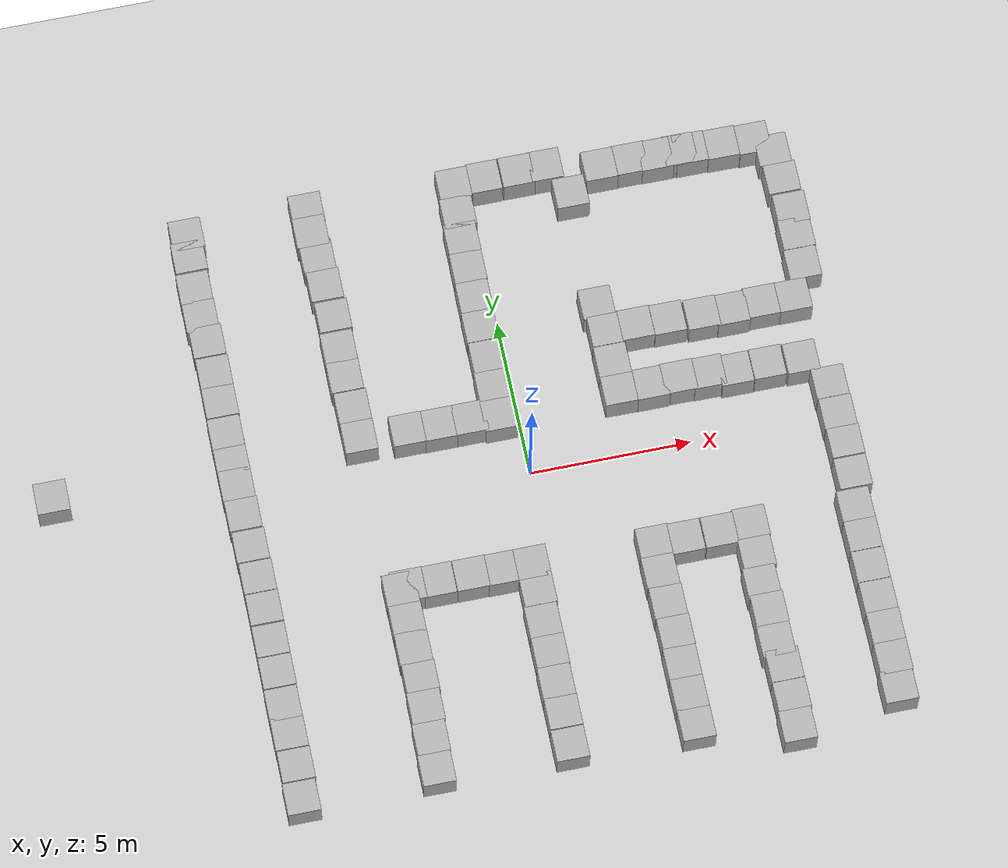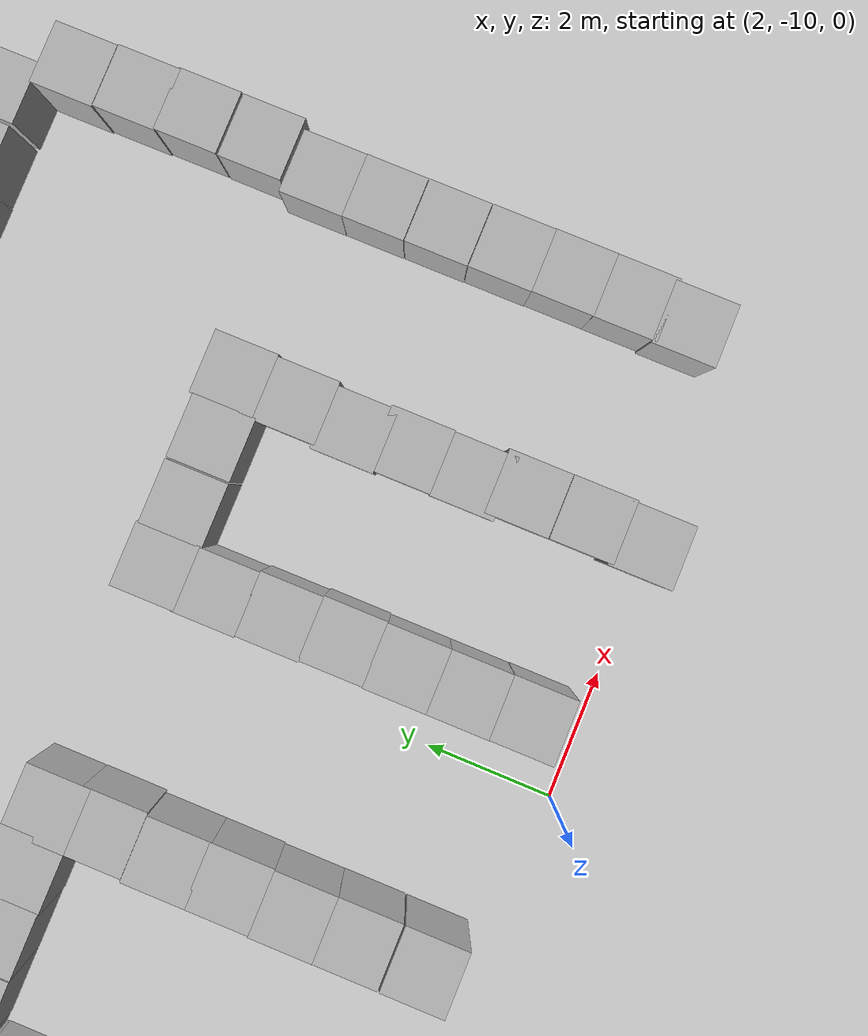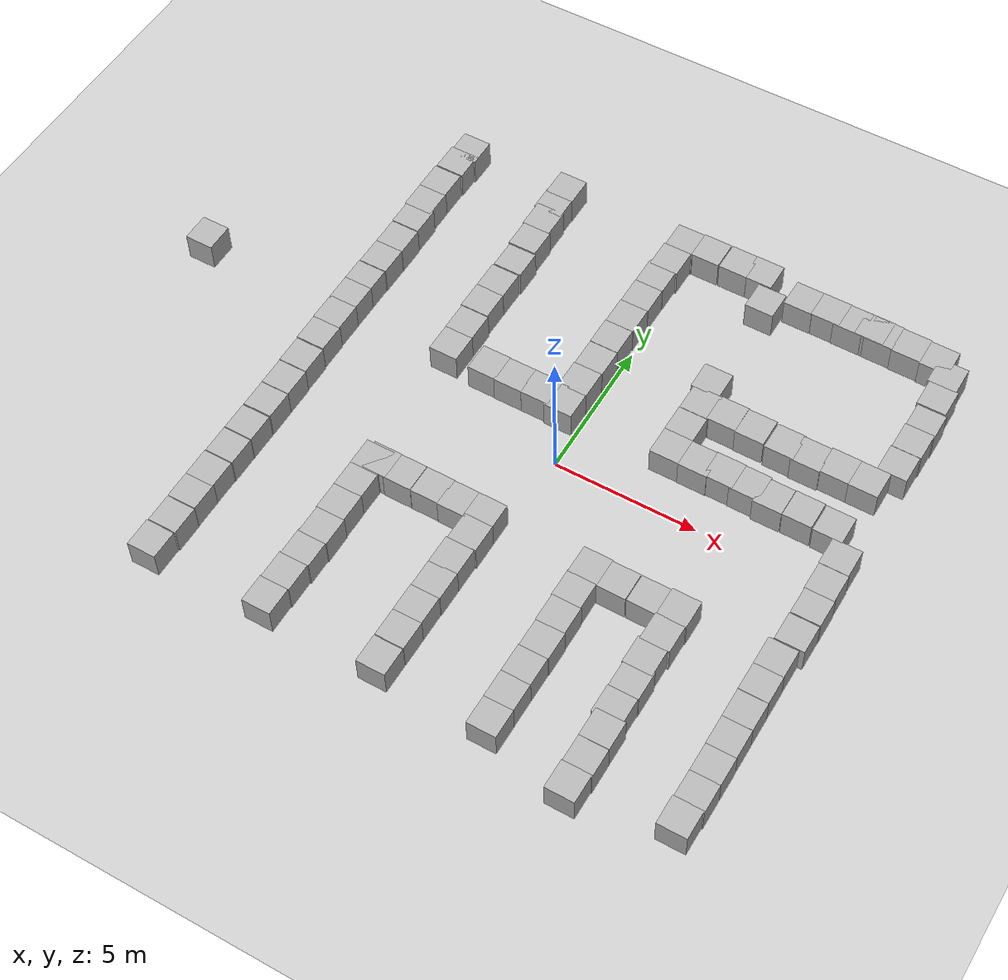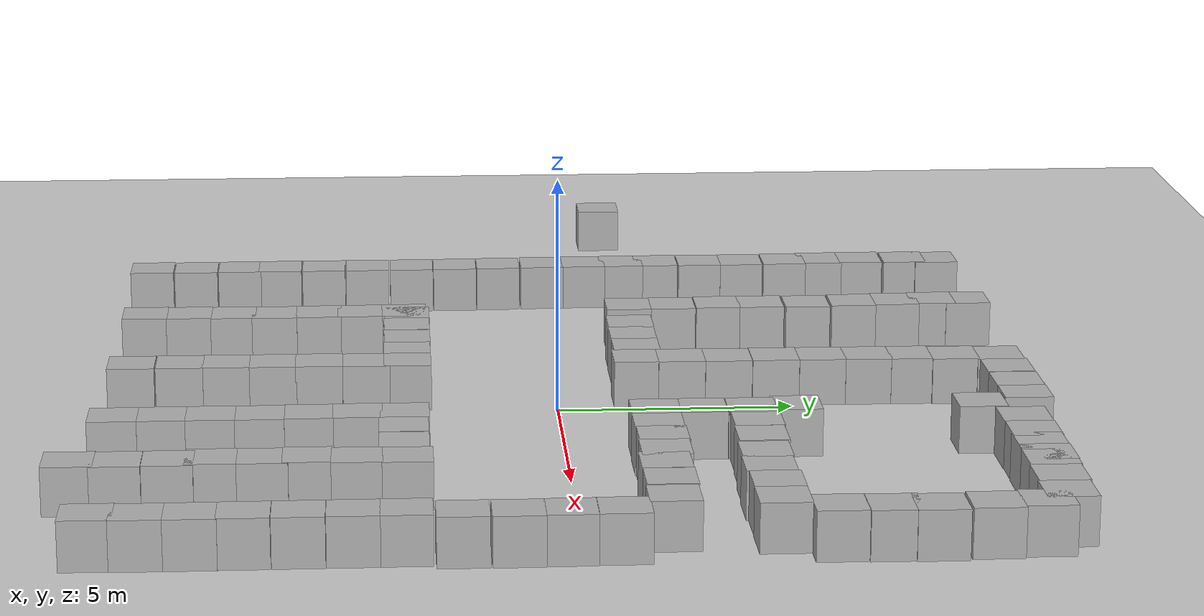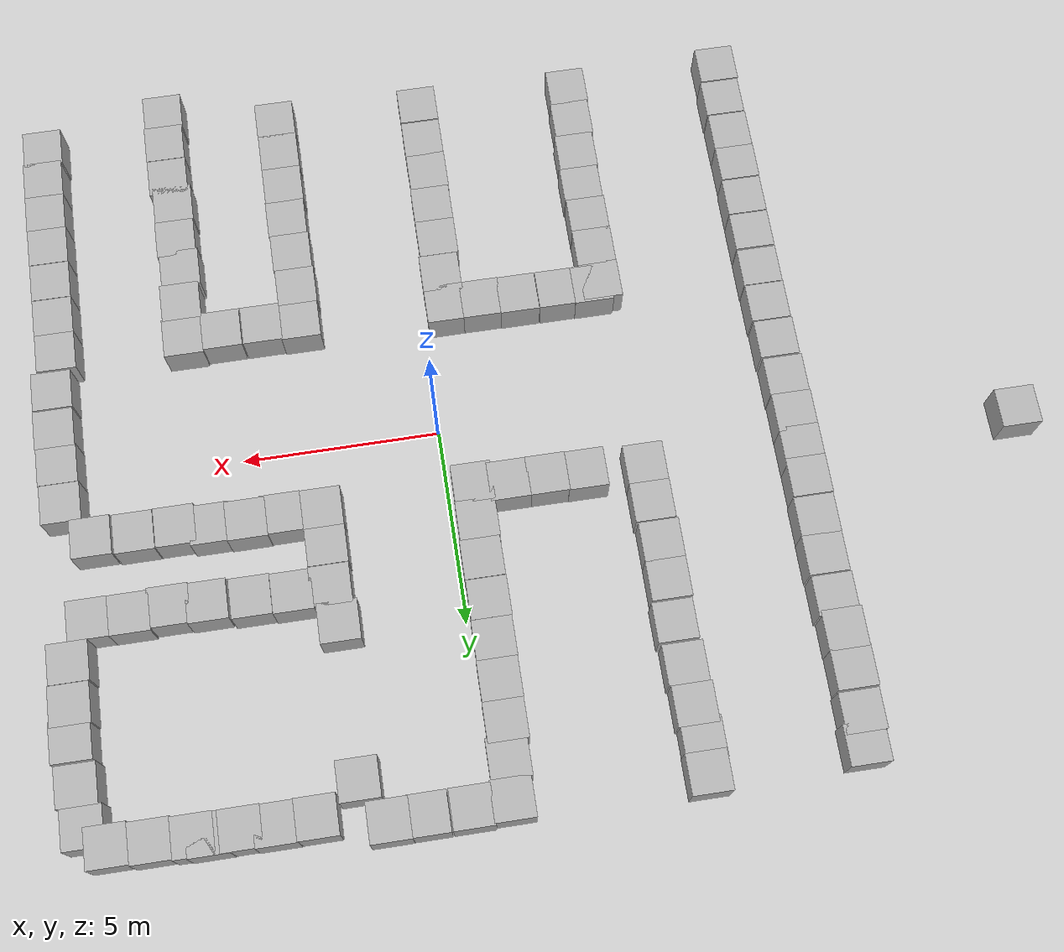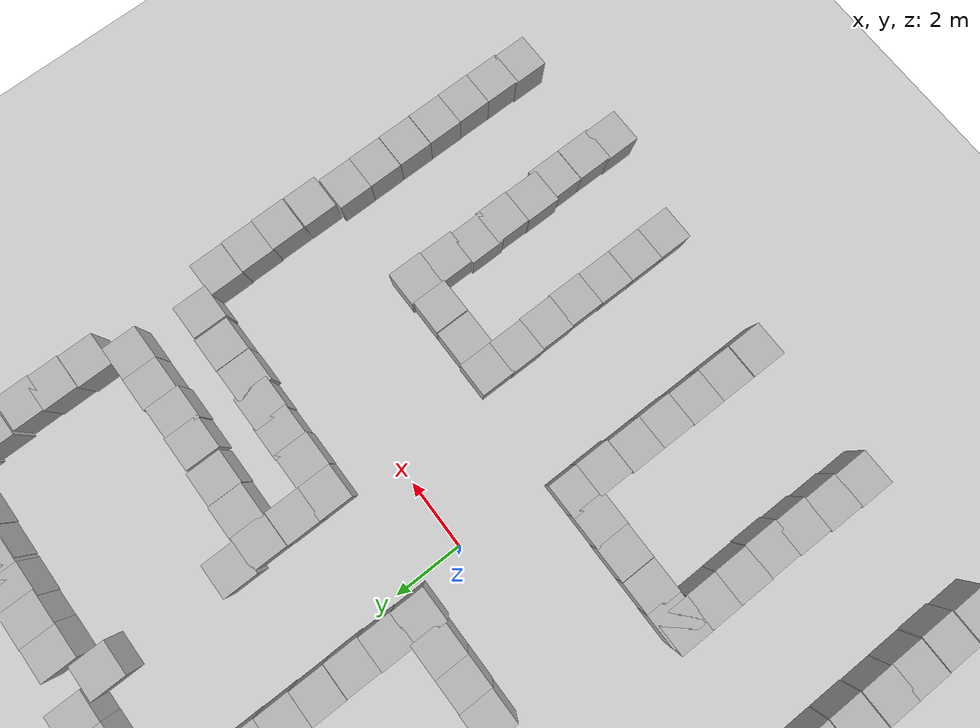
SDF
<?xml version='1.0' encoding='utf-8'?>
<sdf version="1.9">
  <world name="empty">
    <physics name="1ms" type="ignored">
      <max_step_size>0.001</max_step_size>
      <real_time_factor>1</real_time_factor>
      <real_time_update_rate>1000</real_time_update_rate>
    </physics>
    <plugin filename="libignition-gazebo-sensors-system.so" name="ignition::gazebo::systems::Sensors">
      <render_engine>ogre2</render_engine>
    </plugin>
    <plugin name="gz::sim::systems::Physics" filename="ignition-gazebo-physics-system" />
    <plugin name="gz::sim::systems::UserCommands" filename="ignition-gazebo-user-commands-system" />
    <plugin name="gz::sim::systems::SceneBroadcaster" filename="ignition-gazebo-scene-broadcaster-system" />
    <plugin name="gz::sim::systems::Contact" filename="ignition-gazebo-contact-system" />
    <gravity>0 0 -9.8</gravity>
    <magnetic_field>6e-06 2.3e-05 -4.2e-05</magnetic_field>
    <atmosphere type="adiabatic" />
    <scene>
      <ambient>0.4 0.4 0.4 1</ambient>
      <background>0.7 0.7 0.7 1</background>
      <shadows>true</shadows>
    </scene>
    <model name="ground_plane">
      <static>true</static>
      <link name="link">
        <collision name="collision">
          <geometry>
            <plane>
              <normal>0 0 1</normal>
              <size>100 100</size>
            </plane>
          </geometry>
          <surface>
            <friction>
              <ode />
            </friction>
            <bounce />
            <contact />
          </surface>
        </collision>
        <visual name="visual">
          <geometry>
            <plane>
              <normal>0 0 1</normal>
              <size>100 100</size>
            </plane>
          </geometry>
          <material>
            <ambient>0.8 0.8 0.8 1</ambient>
            <diffuse>0.8 0.8 0.8 1</diffuse>
            <specular>0.8 0.8 0.8 1</specular>
          </material>
        </visual>
        <pose>0 0 0 0 -0 0</pose>
        <inertial>
          <pose>0 0 0 0 -0 0</pose>
          <mass>1</mass>
          <inertia>
            <ixx>1</ixx>
            <ixy>0</ixy>
            <ixz>0</ixz>
            <iyy>1</iyy>
            <iyz>0</iyz>
            <izz>1</izz>
          </inertia>
        </inertial>
        <enable_wind>false</enable_wind>
      </link>
      <pose>0 0 0 0 -0 0</pose>
      <self_collide>false</self_collide>
    </model>
    <light name="sun" type="directional">
      <pose>0 0 10 0 -0 0</pose>
      <cast_shadows>true</cast_shadows>
      <intensity>1</intensity>
      <direction>-0.5 0.1 -0.9</direction>
      <diffuse>0.8 0.8 0.8 1</diffuse>
      <specular>0.2 0.2 0.2 1</specular>
      <attenuation>
        <range>1000</range>
        <linear>0.01</linear>
        <constant>0.90000000000000002</constant>
        <quadratic>0.001</quadratic>
      </attenuation>
      <spot>
        <inner_angle>0</inner_angle>
        <outer_angle>0</outer_angle>
        <falloff>0</falloff>
      </spot>
    </light>
    <model name="ziekenhuis_walls">
      <pose>0 0 0 0 0 0</pose>
      <static>true</static>
      <link name="wall_0">
        <pose>-0.628622 -3.17576 0.5 0 -0 0</pose>
        <visual name="visual_0">
          <geometry>
            <box>
              <size>1 1 1</size>
            </box>
          </geometry>
          <material>
            <ambient>0.3 0.3 0.3 1</ambient>
            <diffuse>0.7 0.7 0.7 1</diffuse>
            <specular>1 1 1 1</specular>
          </material>
        </visual>
        <collision name="collision_0">
          <geometry>
            <box>
              <size>1 1 1</size>
            </box>
          </geometry>
          <surface>
            <friction>
              <ode />
            </friction>
            <bounce />
            <contact />
          </surface>
        </collision>
      </link>
      <link name="wall_1">
        <pose>-1.54573 -3.17539 0.5 0 -0 0</pose>
        <visual name="visual_1">
          <geometry>
            <box>
              <size>1 1 1</size>
            </box>
          </geometry>
          <material>
            <ambient>0.3 0.3 0.3 1</ambient>
            <diffuse>0.7 0.7 0.7 1</diffuse>
            <specular>1 1 1 1</specular>
          </material>
        </visual>
        <collision name="collision_1">
          <geometry>
            <box>
              <size>1 1 1</size>
            </box>
          </geometry>
          <surface>
            <friction>
              <ode />
            </friction>
            <bounce />
            <contact />
          </surface>
        </collision>
      </link>
      <link name="wall_2">
        <pose>-2.50675 -3.16277 0.5 0 -0 0</pose>
        <visual name="visual_2">
          <geometry>
            <box>
              <size>1 1 1</size>
            </box>
          </geometry>
          <material>
            <ambient>0.3 0.3 0.3 1</ambient>
            <diffuse>0.7 0.7 0.7 1</diffuse>
            <specular>1 1 1 1</specular>
          </material>
        </visual>
        <collision name="collision_2">
          <geometry>
            <box>
              <size>1 1 1</size>
            </box>
          </geometry>
          <surface>
            <friction>
              <ode />
            </friction>
            <bounce />
            <contact />
          </surface>
        </collision>
      </link>
      <link name="wall_3">
        <pose>-3.51964 -3.15896 0.5 0 -0 0</pose>
        <visual name="visual_3">
          <geometry>
            <box>
              <size>1 1 1</size>
            </box>
          </geometry>
          <material>
            <ambient>0.3 0.3 0.3 1</ambient>
            <diffuse>0.7 0.7 0.7 1</diffuse>
            <specular>1 1 1 1</specular>
          </material>
        </visual>
        <collision name="collision_3">
          <geometry>
            <box>
              <size>1 1 1</size>
            </box>
          </geometry>
          <surface>
            <friction>
              <ode />
            </friction>
            <bounce />
            <contact />
          </surface>
        </collision>
      </link>
      <link name="wall_4">
        <pose>-4.44088 -3.14907 0.5 0 -0 0</pose>
        <visual name="visual_4">
          <geometry>
            <box>
              <size>1 1 1</size>
            </box>
          </geometry>
          <material>
            <ambient>0.3 0.3 0.3 1</ambient>
            <diffuse>0.7 0.7 0.7 1</diffuse>
            <specular>1 1 1 1</specular>
          </material>
        </visual>
        <collision name="collision_4">
          <geometry>
            <box>
              <size>1 1 1</size>
            </box>
          </geometry>
          <surface>
            <friction>
              <ode />
            </friction>
            <bounce />
            <contact />
          </surface>
        </collision>
      </link>
      <link name="wall_5">
        <pose>-14.46258 1.78849 0.5 0 -0 0</pose>
        <visual name="visual_5">
          <geometry>
            <box>
              <size>1 1 1</size>
            </box>
          </geometry>
          <material>
            <ambient>0.3 0.3 0.3 1</ambient>
            <diffuse>0.7 0.7 0.7 1</diffuse>
            <specular>1 1 1 1</specular>
          </material>
        </visual>
        <collision name="collision_5">
          <geometry>
            <box>
              <size>1 1 1</size>
            </box>
          </geometry>
          <surface>
            <friction>
              <ode />
            </friction>
            <bounce />
            <contact />
          </surface>
        </collision>
      </link>
      <link name="wall_6">
        <pose>-3.47193 1.7902 0.5 0 -0 0</pose>
        <visual name="visual_6">
          <geometry>
            <box>
              <size>1 1 1</size>
            </box>
          </geometry>
          <material>
            <ambient>0.3 0.3 0.3 1</ambient>
            <diffuse>0.7 0.7 0.7 1</diffuse>
            <specular>1 1 1 1</specular>
          </material>
        </visual>
        <collision name="collision_6">
          <geometry>
            <box>
              <size>1 1 1</size>
            </box>
          </geometry>
          <surface>
            <friction>
              <ode />
            </friction>
            <bounce />
            <contact />
          </surface>
        </collision>
      </link>
      <link name="wall_7">
        <pose>-2.5012 1.77664 0.5 0 -0 0</pose>
        <visual name="visual_7">
          <geometry>
            <box>
              <size>1 1 1</size>
            </box>
          </geometry>
          <material>
            <ambient>0.3 0.3 0.3 1</ambient>
            <diffuse>0.7 0.7 0.7 1</diffuse>
            <specular>1 1 1 1</specular>
          </material>
        </visual>
        <collision name="collision_7">
          <geometry>
            <box>
              <size>1 1 1</size>
            </box>
          </geometry>
          <surface>
            <friction>
              <ode />
            </friction>
            <bounce />
            <contact />
          </surface>
        </collision>
      </link>
      <link name="wall_8">
        <pose>-1.52755 1.77711 0.5 0 -0 0</pose>
        <visual name="visual_8">
          <geometry>
            <box>
              <size>1 1 1</size>
            </box>
          </geometry>
          <material>
            <ambient>0.3 0.3 0.3 1</ambient>
            <diffuse>0.7 0.7 0.7 1</diffuse>
            <specular>1 1 1 1</specular>
          </material>
        </visual>
        <collision name="collision_8">
          <geometry>
            <box>
              <size>1 1 1</size>
            </box>
          </geometry>
          <surface>
            <friction>
              <ode />
            </friction>
            <bounce />
            <contact />
          </surface>
        </collision>
      </link>
      <link name="wall_9">
        <pose>-0.640154 1.71751 0.5 0 -0 0</pose>
        <visual name="visual_9">
          <geometry>
            <box>
              <size>1 1 1</size>
            </box>
          </geometry>
          <material>
            <ambient>0.3 0.3 0.3 1</ambient>
            <diffuse>0.7 0.7 0.7 1</diffuse>
            <specular>1 1 1 1</specular>
          </material>
        </visual>
        <collision name="collision_9">
          <geometry>
            <box>
              <size>1 1 1</size>
            </box>
          </geometry>
          <surface>
            <friction>
              <ode />
            </friction>
            <bounce />
            <contact />
          </surface>
        </collision>
      </link>
      <link name="wall_10">
        <pose>-0.624925 -4.05306 0.5 0 -0 0</pose>
        <visual name="visual_10">
          <geometry>
            <box>
              <size>1 1 1</size>
            </box>
          </geometry>
          <material>
            <ambient>0.3 0.3 0.3 1</ambient>
            <diffuse>0.7 0.7 0.7 1</diffuse>
            <specular>1 1 1 1</specular>
          </material>
        </visual>
        <collision name="collision_10">
          <geometry>
            <box>
              <size>1 1 1</size>
            </box>
          </geometry>
          <surface>
            <friction>
              <ode />
            </friction>
            <bounce />
            <contact />
          </surface>
        </collision>
      </link>
      <link name="wall_11">
        <pose>-0.666125 -5.05588 0.5 0 -0 0</pose>
        <visual name="visual_11">
          <geometry>
            <box>
              <size>1 1 1</size>
            </box>
          </geometry>
          <material>
            <ambient>0.3 0.3 0.3 1</ambient>
            <diffuse>0.7 0.7 0.7 1</diffuse>
            <specular>1 1 1 1</specular>
          </material>
        </visual>
        <collision name="collision_11">
          <geometry>
            <box>
              <size>1 1 1</size>
            </box>
          </geometry>
          <surface>
            <friction>
              <ode />
            </friction>
            <bounce />
            <contact />
          </surface>
        </collision>
      </link>
      <link name="wall_12">
        <pose>-0.666125 -6.02587 0.5 0 -0 0</pose>
        <visual name="visual_12">
          <geometry>
            <box>
              <size>1 1 1</size>
            </box>
          </geometry>
          <material>
            <ambient>0.3 0.3 0.3 1</ambient>
            <diffuse>0.7 0.7 0.7 1</diffuse>
            <specular>1 1 1 1</specular>
          </material>
        </visual>
        <collision name="collision_12">
          <geometry>
            <box>
              <size>1 1 1</size>
            </box>
          </geometry>
          <surface>
            <friction>
              <ode />
            </friction>
            <bounce />
            <contact />
          </surface>
        </collision>
      </link>
      <link name="wall_13">
        <pose>-0.682233 -7.0253 0.5 0 -0 0</pose>
        <visual name="visual_13">
          <geometry>
            <box>
              <size>1 1 1</size>
            </box>
          </geometry>
          <material>
            <ambient>0.3 0.3 0.3 1</ambient>
            <diffuse>0.7 0.7 0.7 1</diffuse>
            <specular>1 1 1 1</specular>
          </material>
        </visual>
        <collision name="collision_13">
          <geometry>
            <box>
              <size>1 1 1</size>
            </box>
          </geometry>
          <surface>
            <friction>
              <ode />
            </friction>
            <bounce />
            <contact />
          </surface>
        </collision>
      </link>
      <link name="wall_14">
        <pose>-0.678292 -8.00642 0.500001 0 -0 0</pose>
        <visual name="visual_14">
          <geometry>
            <box>
              <size>1 1 1</size>
            </box>
          </geometry>
          <material>
            <ambient>0.3 0.3 0.3 1</ambient>
            <diffuse>0.7 0.7 0.7 1</diffuse>
            <specular>1 1 1 1</specular>
          </material>
        </visual>
        <collision name="collision_14">
          <geometry>
            <box>
              <size>1 1 1</size>
            </box>
          </geometry>
          <surface>
            <friction>
              <ode />
            </friction>
            <bounce />
            <contact />
          </surface>
        </collision>
      </link>
      <link name="wall_15">
        <pose>-0.682523 -9.03062 0.5 0 -0 0</pose>
        <visual name="visual_15">
          <geometry>
            <box>
              <size>1 1 1</size>
            </box>
          </geometry>
          <material>
            <ambient>0.3 0.3 0.3 1</ambient>
            <diffuse>0.7 0.7 0.7 1</diffuse>
            <specular>1 1 1 1</specular>
          </material>
        </visual>
        <collision name="collision_15">
          <geometry>
            <box>
              <size>1 1 1</size>
            </box>
          </geometry>
          <surface>
            <friction>
              <ode />
            </friction>
            <bounce />
            <contact />
          </surface>
        </collision>
      </link>
      <link name="wall_16">
        <pose>-0.62645 2.66518 0.5 0 -0 0</pose>
        <visual name="visual_16">
          <geometry>
            <box>
              <size>1 1 1</size>
            </box>
          </geometry>
          <material>
            <ambient>0.3 0.3 0.3 1</ambient>
            <diffuse>0.7 0.7 0.7 1</diffuse>
            <specular>1 1 1 1</specular>
          </material>
        </visual>
        <collision name="collision_16">
          <geometry>
            <box>
              <size>1 1 1</size>
            </box>
          </geometry>
          <surface>
            <friction>
              <ode />
            </friction>
            <bounce />
            <contact />
          </surface>
        </collision>
      </link>
      <link name="wall_17">
        <pose>-0.602355 3.6627 0.5 0 -0 0</pose>
        <visual name="visual_17">
          <geometry>
            <box>
              <size>1 1 1</size>
            </box>
          </geometry>
          <material>
            <ambient>0.3 0.3 0.3 1</ambient>
            <diffuse>0.7 0.7 0.7 1</diffuse>
            <specular>1 1 1 1</specular>
          </material>
        </visual>
        <collision name="collision_17">
          <geometry>
            <box>
              <size>1 1 1</size>
            </box>
          </geometry>
          <surface>
            <friction>
              <ode />
            </friction>
            <bounce />
            <contact />
          </surface>
        </collision>
      </link>
      <link name="wall_18">
        <pose>-0.610927 4.67319 0.5 0 -0 0</pose>
        <visual name="visual_18">
          <geometry>
            <box>
              <size>1 1 1</size>
            </box>
          </geometry>
          <material>
            <ambient>0.3 0.3 0.3 1</ambient>
            <diffuse>0.7 0.7 0.7 1</diffuse>
            <specular>1 1 1 1</specular>
          </material>
        </visual>
        <collision name="collision_18">
          <geometry>
            <box>
              <size>1 1 1</size>
            </box>
          </geometry>
          <surface>
            <friction>
              <ode />
            </friction>
            <bounce />
            <contact />
          </surface>
        </collision>
      </link>
      <link name="wall_19">
        <pose>-0.595787 5.67413 0.5 0 -0 0</pose>
        <visual name="visual_19">
          <geometry>
            <box>
              <size>1 1 1</size>
            </box>
          </geometry>
          <material>
            <ambient>0.3 0.3 0.3 1</ambient>
            <diffuse>0.7 0.7 0.7 1</diffuse>
            <specular>1 1 1 1</specular>
          </material>
        </visual>
        <collision name="collision_19">
          <geometry>
            <box>
              <size>1 1 1</size>
            </box>
          </geometry>
          <surface>
            <friction>
              <ode />
            </friction>
            <bounce />
            <contact />
          </surface>
        </collision>
      </link>
      <link name="wall_20">
        <pose>-0.583933 6.66382 0.5 0 -0 0</pose>
        <visual name="visual_20">
          <geometry>
            <box>
              <size>1 1 1</size>
            </box>
          </geometry>
          <material>
            <ambient>0.3 0.3 0.3 1</ambient>
            <diffuse>0.7 0.7 0.7 1</diffuse>
            <specular>1 1 1 1</specular>
          </material>
        </visual>
        <collision name="collision_20">
          <geometry>
            <box>
              <size>1 1 1</size>
            </box>
          </geometry>
          <surface>
            <friction>
              <ode />
            </friction>
            <bounce />
            <contact />
          </surface>
        </collision>
      </link>
      <link name="wall_21">
        <pose>-0.575678 7.6423 0.5 0 -0 0</pose>
        <visual name="visual_21">
          <geometry>
            <box>
              <size>1 1 1</size>
            </box>
          </geometry>
          <material>
            <ambient>0.3 0.3 0.3 1</ambient>
            <diffuse>0.7 0.7 0.7 1</diffuse>
            <specular>1 1 1 1</specular>
          </material>
        </visual>
        <collision name="collision_21">
          <geometry>
            <box>
              <size>1 1 1</size>
            </box>
          </geometry>
          <surface>
            <friction>
              <ode />
            </friction>
            <bounce />
            <contact />
          </surface>
        </collision>
      </link>
      <link name="wall_22">
        <pose>3.11918 -3.27527 0.5 0 -0 0</pose>
        <visual name="visual_22">
          <geometry>
            <box>
              <size>1 1 1</size>
            </box>
          </geometry>
          <material>
            <ambient>0.3 0.3 0.3 1</ambient>
            <diffuse>0.7 0.7 0.7 1</diffuse>
            <specular>1 1 1 1</specular>
          </material>
        </visual>
        <collision name="collision_22">
          <geometry>
            <box>
              <size>1 1 1</size>
            </box>
          </geometry>
          <surface>
            <friction>
              <ode />
            </friction>
            <bounce />
            <contact />
          </surface>
        </collision>
      </link>
      <link name="wall_23">
        <pose>3.10814 -4.22657 0.5 0 -0 0</pose>
        <visual name="visual_23">
          <geometry>
            <box>
              <size>1 1 1</size>
            </box>
          </geometry>
          <material>
            <ambient>0.3 0.3 0.3 1</ambient>
            <diffuse>0.7 0.7 0.7 1</diffuse>
            <specular>1 1 1 1</specular>
          </material>
        </visual>
        <collision name="collision_23">
          <geometry>
            <box>
              <size>1 1 1</size>
            </box>
          </geometry>
          <surface>
            <friction>
              <ode />
            </friction>
            <bounce />
            <contact />
          </surface>
        </collision>
      </link>
      <link name="wall_24">
        <pose>3.12982 -5.21504 0.5 0 -0 0</pose>
        <visual name="visual_24">
          <geometry>
            <box>
              <size>1 1 1</size>
            </box>
          </geometry>
          <material>
            <ambient>0.3 0.3 0.3 1</ambient>
            <diffuse>0.7 0.7 0.7 1</diffuse>
            <specular>1 1 1 1</specular>
          </material>
        </visual>
        <collision name="collision_24">
          <geometry>
            <box>
              <size>1 1 1</size>
            </box>
          </geometry>
          <surface>
            <friction>
              <ode />
            </friction>
            <bounce />
            <contact />
          </surface>
        </collision>
      </link>
      <link name="wall_25">
        <pose>3.15098 -6.19862 0.5 0 -0 0</pose>
        <visual name="visual_25">
          <geometry>
            <box>
              <size>1 1 1</size>
            </box>
          </geometry>
          <material>
            <ambient>0.3 0.3 0.3 1</ambient>
            <diffuse>0.7 0.7 0.7 1</diffuse>
            <specular>1 1 1 1</specular>
          </material>
        </visual>
        <collision name="collision_25">
          <geometry>
            <box>
              <size>1 1 1</size>
            </box>
          </geometry>
          <surface>
            <friction>
              <ode />
            </friction>
            <bounce />
            <contact />
          </surface>
        </collision>
      </link>
      <link name="wall_26">
        <pose>3.13753 -7.18844 0.5 0 -0 0</pose>
        <visual name="visual_26">
          <geometry>
            <box>
              <size>1 1 1</size>
            </box>
          </geometry>
          <material>
            <ambient>0.3 0.3 0.3 1</ambient>
            <diffuse>0.7 0.7 0.7 1</diffuse>
            <specular>1 1 1 1</specular>
          </material>
        </visual>
        <collision name="collision_26">
          <geometry>
            <box>
              <size>1 1 1</size>
            </box>
          </geometry>
          <surface>
            <friction>
              <ode />
            </friction>
            <bounce />
            <contact />
          </surface>
        </collision>
      </link>
      <link name="wall_27">
        <pose>3.13773 -8.18491 0.5 0 -0 0</pose>
        <visual name="visual_27">
          <geometry>
            <box>
              <size>1 1 1</size>
            </box>
          </geometry>
          <material>
            <ambient>0.3 0.3 0.3 1</ambient>
            <diffuse>0.7 0.7 0.7 1</diffuse>
            <specular>1 1 1 1</specular>
          </material>
        </visual>
        <collision name="collision_27">
          <geometry>
            <box>
              <size>1 1 1</size>
            </box>
          </geometry>
          <surface>
            <friction>
              <ode />
            </friction>
            <bounce />
            <contact />
          </surface>
        </collision>
      </link>
      <link name="wall_28">
        <pose>3.14306 -9.15602 0.5 0 -0 0</pose>
        <visual name="visual_28">
          <geometry>
            <box>
              <size>1 1 1</size>
            </box>
          </geometry>
          <material>
            <ambient>0.3 0.3 0.3 1</ambient>
            <diffuse>0.7 0.7 0.7 1</diffuse>
            <specular>1 1 1 1</specular>
          </material>
        </visual>
        <collision name="collision_28">
          <geometry>
            <box>
              <size>1 1 1</size>
            </box>
          </geometry>
          <surface>
            <friction>
              <ode />
            </friction>
            <bounce />
            <contact />
          </surface>
        </collision>
      </link>
      <link name="wall_29">
        <pose>3.11958 1.81014 0.5 0 -0 0</pose>
        <visual name="visual_29">
          <geometry>
            <box>
              <size>1 1 1</size>
            </box>
          </geometry>
          <material>
            <ambient>0.3 0.3 0.3 1</ambient>
            <diffuse>0.7 0.7 0.7 1</diffuse>
            <specular>1 1 1 1</specular>
          </material>
        </visual>
        <collision name="collision_29">
          <geometry>
            <box>
              <size>1 1 1</size>
            </box>
          </geometry>
          <surface>
            <friction>
              <ode />
            </friction>
            <bounce />
            <contact />
          </surface>
        </collision>
      </link>
      <link name="wall_30">
        <pose>3.11744 2.76434 0.5 0 -0 0</pose>
        <visual name="visual_30">
          <geometry>
            <box>
              <size>1 1 1</size>
            </box>
          </geometry>
          <material>
            <ambient>0.3 0.3 0.3 1</ambient>
            <diffuse>0.7 0.7 0.7 1</diffuse>
            <specular>1 1 1 1</specular>
          </material>
        </visual>
        <collision name="collision_30">
          <geometry>
            <box>
              <size>1 1 1</size>
            </box>
          </geometry>
          <surface>
            <friction>
              <ode />
            </friction>
            <bounce />
            <contact />
          </surface>
        </collision>
      </link>
      <link name="wall_31">
        <pose>3.13123 3.77565 0.5 0 -0 0</pose>
        <visual name="visual_31">
          <geometry>
            <box>
              <size>1 1 1</size>
            </box>
          </geometry>
          <material>
            <ambient>0.3 0.3 0.3 1</ambient>
            <diffuse>0.7 0.7 0.7 1</diffuse>
            <specular>1 1 1 1</specular>
          </material>
        </visual>
        <collision name="collision_31">
          <geometry>
            <box>
              <size>1 1 1</size>
            </box>
          </geometry>
          <surface>
            <friction>
              <ode />
            </friction>
            <bounce />
            <contact />
          </surface>
        </collision>
      </link>
      <link name="wall_32">
        <pose>3.02328 8.49449 0.5 0 -0 0</pose>
        <visual name="visual_32">
          <geometry>
            <box>
              <size>1 1 1</size>
            </box>
          </geometry>
          <material>
            <ambient>0.3 0.3 0.3 1</ambient>
            <diffuse>0.7 0.7 0.7 1</diffuse>
            <specular>1 1 1 1</specular>
          </material>
        </visual>
        <collision name="collision_32">
          <geometry>
            <box>
              <size>1 1 1</size>
            </box>
          </geometry>
          <surface>
            <friction>
              <ode />
            </friction>
            <bounce />
            <contact />
          </surface>
        </collision>
      </link>
      <link name="wall_33">
        <pose>-0.51947 8.52309 0.5 0 -0 0</pose>
        <visual name="visual_33">
          <geometry>
            <box>
              <size>1 1 1</size>
            </box>
          </geometry>
          <material>
            <ambient>0.3 0.3 0.3 1</ambient>
            <diffuse>0.7 0.7 0.7 1</diffuse>
            <specular>1 1 1 1</specular>
          </material>
        </visual>
        <collision name="collision_33">
          <geometry>
            <box>
              <size>1 1 1</size>
            </box>
          </geometry>
          <surface>
            <friction>
              <ode />
            </friction>
            <bounce />
            <contact />
          </surface>
        </collision>
      </link>
      <link name="wall_34">
        <pose>-0.473583 9.48528 0.5 0 -0 0</pose>
        <visual name="visual_34">
          <geometry>
            <box>
              <size>1 1 1</size>
            </box>
          </geometry>
          <material>
            <ambient>0.3 0.3 0.3 1</ambient>
            <diffuse>0.7 0.7 0.7 1</diffuse>
            <specular>1 1 1 1</specular>
          </material>
        </visual>
        <collision name="collision_34">
          <geometry>
            <box>
              <size>1 1 1</size>
            </box>
          </geometry>
          <surface>
            <friction>
              <ode />
            </friction>
            <bounce />
            <contact />
          </surface>
        </collision>
      </link>
      <link name="wall_35">
        <pose>0.491718 9.52437 0.5 0 -0 0</pose>
        <visual name="visual_35">
          <geometry>
            <box>
              <size>1 1 1</size>
            </box>
          </geometry>
          <material>
            <ambient>0.3 0.3 0.3 1</ambient>
            <diffuse>0.7 0.7 0.7 1</diffuse>
            <specular>1 1 1 1</specular>
          </material>
        </visual>
        <collision name="collision_35">
          <geometry>
            <box>
              <size>1 1 1</size>
            </box>
          </geometry>
          <surface>
            <friction>
              <ode />
            </friction>
            <bounce />
            <contact />
          </surface>
        </collision>
      </link>
      <link name="wall_36">
        <pose>1.52596 9.52964 0.5 0 -0 0</pose>
        <visual name="visual_36">
          <geometry>
            <box>
              <size>1 1 1</size>
            </box>
          </geometry>
          <material>
            <ambient>0.3 0.3 0.3 1</ambient>
            <diffuse>0.7 0.7 0.7 1</diffuse>
            <specular>1 1 1 1</specular>
          </material>
        </visual>
        <collision name="collision_36">
          <geometry>
            <box>
              <size>1 1 1</size>
            </box>
          </geometry>
          <surface>
            <friction>
              <ode />
            </friction>
            <bounce />
            <contact />
          </surface>
        </collision>
      </link>
      <link name="wall_37">
        <pose>2.43308 9.5376 0.5 0 -0 0</pose>
        <visual name="visual_37">
          <geometry>
            <box>
              <size>1 1 1</size>
            </box>
          </geometry>
          <material>
            <ambient>0.3 0.3 0.3 1</ambient>
            <diffuse>0.7 0.7 0.7 1</diffuse>
            <specular>1 1 1 1</specular>
          </material>
        </visual>
        <collision name="collision_37">
          <geometry>
            <box>
              <size>1 1 1</size>
            </box>
          </geometry>
          <surface>
            <friction>
              <ode />
            </friction>
            <bounce />
            <contact />
          </surface>
        </collision>
      </link>
      <link name="wall_38">
        <pose>4.10268 -3.30615 0.5 0 -0 0</pose>
        <visual name="visual_38">
          <geometry>
            <box>
              <size>1 1 1</size>
            </box>
          </geometry>
          <material>
            <ambient>0.3 0.3 0.3 1</ambient>
            <diffuse>0.7 0.7 0.7 1</diffuse>
            <specular>1 1 1 1</specular>
          </material>
        </visual>
        <collision name="collision_38">
          <geometry>
            <box>
              <size>1 1 1</size>
            </box>
          </geometry>
          <surface>
            <friction>
              <ode />
            </friction>
            <bounce />
            <contact />
          </surface>
        </collision>
      </link>
      <link name="wall_39">
        <pose>5.12914 -3.30697 0.5 0 -0 0</pose>
        <visual name="visual_39">
          <geometry>
            <box>
              <size>1 1 1</size>
            </box>
          </geometry>
          <material>
            <ambient>0.3 0.3 0.3 1</ambient>
            <diffuse>0.7 0.7 0.7 1</diffuse>
            <specular>1 1 1 1</specular>
          </material>
        </visual>
        <collision name="collision_39">
          <geometry>
            <box>
              <size>1 1 1</size>
            </box>
          </geometry>
          <surface>
            <friction>
              <ode />
            </friction>
            <bounce />
            <contact />
          </surface>
        </collision>
      </link>
      <link name="wall_40">
        <pose>6.11725 -3.25256 0.5 0 -0 0</pose>
        <visual name="visual_40">
          <geometry>
            <box>
              <size>1 1 1</size>
            </box>
          </geometry>
          <material>
            <ambient>0.3 0.3 0.3 1</ambient>
            <diffuse>0.7 0.7 0.7 1</diffuse>
            <specular>1 1 1 1</specular>
          </material>
        </visual>
        <collision name="collision_40">
          <geometry>
            <box>
              <size>1 1 1</size>
            </box>
          </geometry>
          <surface>
            <friction>
              <ode />
            </friction>
            <bounce />
            <contact />
          </surface>
        </collision>
      </link>
      <link name="wall_41">
        <pose>6.08814 -4.23526 0.5 0 -0 0</pose>
        <visual name="visual_41">
          <geometry>
            <box>
              <size>1 1 1</size>
            </box>
          </geometry>
          <material>
            <ambient>0.3 0.3 0.3 1</ambient>
            <diffuse>0.7 0.7 0.7 1</diffuse>
            <specular>1 1 1 1</specular>
          </material>
        </visual>
        <collision name="collision_41">
          <geometry>
            <box>
              <size>1 1 1</size>
            </box>
          </geometry>
          <surface>
            <friction>
              <ode />
            </friction>
            <bounce />
            <contact />
          </surface>
        </collision>
      </link>
      <link name="wall_42">
        <pose>9.34735 -3.31674 0.5 0 -0 0</pose>
        <visual name="visual_42">
          <geometry>
            <box>
              <size>1 1 1</size>
            </box>
          </geometry>
          <material>
            <ambient>0.3 0.3 0.3 1</ambient>
            <diffuse>0.7 0.7 0.7 1</diffuse>
            <specular>1 1 1 1</specular>
          </material>
        </visual>
        <collision name="collision_42">
          <geometry>
            <box>
              <size>1 1 1</size>
            </box>
          </geometry>
          <surface>
            <friction>
              <ode />
            </friction>
            <bounce />
            <contact />
          </surface>
        </collision>
      </link>
      <link name="wall_43">
        <pose>6.02668 -5.18071 0.5 0 -0 0</pose>
        <visual name="visual_43">
          <geometry>
            <box>
              <size>1 1 1</size>
            </box>
          </geometry>
          <material>
            <ambient>0.3 0.3 0.3 1</ambient>
            <diffuse>0.7 0.7 0.7 1</diffuse>
            <specular>1 1 1 1</specular>
          </material>
        </visual>
        <collision name="collision_43">
          <geometry>
            <box>
              <size>1 1 1</size>
            </box>
          </geometry>
          <surface>
            <friction>
              <ode />
            </friction>
            <bounce />
            <contact />
          </surface>
        </collision>
      </link>
      <link name="wall_44">
        <pose>6.06456 -6.05794 0.5 0 -0 0</pose>
        <visual name="visual_44">
          <geometry>
            <box>
              <size>1 1 1</size>
            </box>
          </geometry>
          <material>
            <ambient>0.3 0.3 0.3 1</ambient>
            <diffuse>0.7 0.7 0.7 1</diffuse>
            <specular>1 1 1 1</specular>
          </material>
        </visual>
        <collision name="collision_44">
          <geometry>
            <box>
              <size>1 1 1</size>
            </box>
          </geometry>
          <surface>
            <friction>
              <ode />
            </friction>
            <bounce />
            <contact />
          </surface>
        </collision>
      </link>
      <link name="wall_45">
        <pose>9.35294 -4.29522 0.5 0 -0 0</pose>
        <visual name="visual_45">
          <geometry>
            <box>
              <size>1 1 1</size>
            </box>
          </geometry>
          <material>
            <ambient>0.3 0.3 0.3 1</ambient>
            <diffuse>0.7 0.7 0.7 1</diffuse>
            <specular>1 1 1 1</specular>
          </material>
        </visual>
        <collision name="collision_45">
          <geometry>
            <box>
              <size>1 1 1</size>
            </box>
          </geometry>
          <surface>
            <friction>
              <ode />
            </friction>
            <bounce />
            <contact />
          </surface>
        </collision>
      </link>
      <link name="wall_46">
        <pose>9.35811 -5.30489 0.5 0 -0 0</pose>
        <visual name="visual_46">
          <geometry>
            <box>
              <size>1 1 1</size>
            </box>
          </geometry>
          <material>
            <ambient>0.3 0.3 0.3 1</ambient>
            <diffuse>0.7 0.7 0.7 1</diffuse>
            <specular>1 1 1 1</specular>
          </material>
        </visual>
        <collision name="collision_46">
          <geometry>
            <box>
              <size>1 1 1</size>
            </box>
          </geometry>
          <surface>
            <friction>
              <ode />
            </friction>
            <bounce />
            <contact />
          </surface>
        </collision>
      </link>
      <link name="wall_47">
        <pose>9.3637 -6.31467 0.5 0 -0 0</pose>
        <visual name="visual_47">
          <geometry>
            <box>
              <size>1 1 1</size>
            </box>
          </geometry>
          <material>
            <ambient>0.3 0.3 0.3 1</ambient>
            <diffuse>0.7 0.7 0.7 1</diffuse>
            <specular>1 1 1 1</specular>
          </material>
        </visual>
        <collision name="collision_47">
          <geometry>
            <box>
              <size>1 1 1</size>
            </box>
          </geometry>
          <surface>
            <friction>
              <ode />
            </friction>
            <bounce />
            <contact />
          </surface>
        </collision>
      </link>
      <link name="wall_48">
        <pose>6.0468 -7.05577 0.5 0 -0 0</pose>
        <visual name="visual_48">
          <geometry>
            <box>
              <size>1 1 1</size>
            </box>
          </geometry>
          <material>
            <ambient>0.3 0.3 0.3 1</ambient>
            <diffuse>0.7 0.7 0.7 1</diffuse>
            <specular>1 1 1 1</specular>
          </material>
        </visual>
        <collision name="collision_48">
          <geometry>
            <box>
              <size>1 1 1</size>
            </box>
          </geometry>
          <surface>
            <friction>
              <ode />
            </friction>
            <bounce />
            <contact />
          </surface>
        </collision>
      </link>
      <link name="wall_49">
        <pose>6.11985 -7.88024 0.5 0 -0 0</pose>
        <visual name="visual_49">
          <geometry>
            <box>
              <size>1 1 1</size>
            </box>
          </geometry>
          <material>
            <ambient>0.3 0.3 0.3 1</ambient>
            <diffuse>0.7 0.7 0.7 1</diffuse>
            <specular>1 1 1 1</specular>
          </material>
        </visual>
        <collision name="collision_49">
          <geometry>
            <box>
              <size>1 1 1</size>
            </box>
          </geometry>
          <surface>
            <friction>
              <ode />
            </friction>
            <bounce />
            <contact />
          </surface>
        </collision>
      </link>
      <link name="wall_50">
        <pose>6.12415 -8.88808 0.5 0 -0 0</pose>
        <visual name="visual_50">
          <geometry>
            <box>
              <size>1 1 1</size>
            </box>
          </geometry>
          <material>
            <ambient>0.3 0.3 0.3 1</ambient>
            <diffuse>0.7 0.7 0.7 1</diffuse>
            <specular>1 1 1 1</specular>
          </material>
        </visual>
        <collision name="collision_50">
          <geometry>
            <box>
              <size>1 1 1</size>
            </box>
          </geometry>
          <surface>
            <friction>
              <ode />
            </friction>
            <bounce />
            <contact />
          </surface>
        </collision>
      </link>
      <link name="wall_51">
        <pose>9.37141 -7.29127 0.5 0 -0 0</pose>
        <visual name="visual_51">
          <geometry>
            <box>
              <size>1 1 1</size>
            </box>
          </geometry>
          <material>
            <ambient>0.3 0.3 0.3 1</ambient>
            <diffuse>0.7 0.7 0.7 1</diffuse>
            <specular>1 1 1 1</specular>
          </material>
        </visual>
        <collision name="collision_51">
          <geometry>
            <box>
              <size>1 1 1</size>
            </box>
          </geometry>
          <surface>
            <friction>
              <ode />
            </friction>
            <bounce />
            <contact />
          </surface>
        </collision>
      </link>
      <link name="wall_52">
        <pose>9.36911 -8.28592 0.5 0 -0 0</pose>
        <visual name="visual_52">
          <geometry>
            <box>
              <size>1 1 1</size>
            </box>
          </geometry>
          <material>
            <ambient>0.3 0.3 0.3 1</ambient>
            <diffuse>0.7 0.7 0.7 1</diffuse>
            <specular>1 1 1 1</specular>
          </material>
        </visual>
        <collision name="collision_52">
          <geometry>
            <box>
              <size>1 1 1</size>
            </box>
          </geometry>
          <surface>
            <friction>
              <ode />
            </friction>
            <bounce />
            <contact />
          </surface>
        </collision>
      </link>
      <link name="wall_53">
        <pose>9.33438 -9.21361 0.5 0 -0 0</pose>
        <visual name="visual_53">
          <geometry>
            <box>
              <size>1 1 1</size>
            </box>
          </geometry>
          <material>
            <ambient>0.3 0.3 0.3 1</ambient>
            <diffuse>0.7 0.7 0.7 1</diffuse>
            <specular>1 1 1 1</specular>
          </material>
        </visual>
        <collision name="collision_53">
          <geometry>
            <box>
              <size>1 1 1</size>
            </box>
          </geometry>
          <surface>
            <friction>
              <ode />
            </friction>
            <bounce />
            <contact />
          </surface>
        </collision>
      </link>
      <link name="wall_54">
        <pose>6.09605 -9.80963 0.5 0 -0 0</pose>
        <visual name="visual_54">
          <geometry>
            <box>
              <size>1 1 1</size>
            </box>
          </geometry>
          <material>
            <ambient>0.3 0.3 0.3 1</ambient>
            <diffuse>0.7 0.7 0.7 1</diffuse>
            <specular>1 1 1 1</specular>
          </material>
        </visual>
        <collision name="collision_54">
          <geometry>
            <box>
              <size>1 1 1</size>
            </box>
          </geometry>
          <surface>
            <friction>
              <ode />
            </friction>
            <bounce />
            <contact />
          </surface>
        </collision>
      </link>
      <link name="wall_55">
        <pose>4.11919 1.79761 0.5 0 -0 0</pose>
        <visual name="visual_55">
          <geometry>
            <box>
              <size>1 1 1</size>
            </box>
          </geometry>
          <material>
            <ambient>0.3 0.3 0.3 1</ambient>
            <diffuse>0.7 0.7 0.7 1</diffuse>
            <specular>1 1 1 1</specular>
          </material>
        </visual>
        <collision name="collision_55">
          <geometry>
            <box>
              <size>1 1 1</size>
            </box>
          </geometry>
          <surface>
            <friction>
              <ode />
            </friction>
            <bounce />
            <contact />
          </surface>
        </collision>
      </link>
      <link name="wall_56">
        <pose>4.99012 1.81929 0.5 0 -0 0</pose>
        <visual name="visual_56">
          <geometry>
            <box>
              <size>1 1 1</size>
            </box>
          </geometry>
          <material>
            <ambient>0.3 0.3 0.3 1</ambient>
            <diffuse>0.7 0.7 0.7 1</diffuse>
            <specular>1 1 1 1</specular>
          </material>
        </visual>
        <collision name="collision_56">
          <geometry>
            <box>
              <size>1 1 1</size>
            </box>
          </geometry>
          <surface>
            <friction>
              <ode />
            </friction>
            <bounce />
            <contact />
          </surface>
        </collision>
      </link>
      <link name="wall_57">
        <pose>5.88812 1.79879 0.5 0 -0 0</pose>
        <visual name="visual_57">
          <geometry>
            <box>
              <size>1 1 1</size>
            </box>
          </geometry>
          <material>
            <ambient>0.3 0.3 0.3 1</ambient>
            <diffuse>0.7 0.7 0.7 1</diffuse>
            <specular>1 1 1 1</specular>
          </material>
        </visual>
        <collision name="collision_57">
          <geometry>
            <box>
              <size>1 1 1</size>
            </box>
          </geometry>
          <surface>
            <friction>
              <ode />
            </friction>
            <bounce />
            <contact />
          </surface>
        </collision>
      </link>
      <link name="wall_58">
        <pose>6.7339 1.72644 0.5 0 -0 0</pose>
        <visual name="visual_58">
          <geometry>
            <box>
              <size>1 1 1</size>
            </box>
          </geometry>
          <material>
            <ambient>0.3 0.3 0.3 1</ambient>
            <diffuse>0.7 0.7 0.7 1</diffuse>
            <specular>1 1 1 1</specular>
          </material>
        </visual>
        <collision name="collision_58">
          <geometry>
            <box>
              <size>1 1 1</size>
            </box>
          </geometry>
          <surface>
            <friction>
              <ode />
            </friction>
            <bounce />
            <contact />
          </surface>
        </collision>
      </link>
      <link name="wall_59">
        <pose>7.74781 1.736 0.5 0 -0 0</pose>
        <visual name="visual_59">
          <geometry>
            <box>
              <size>1 1 1</size>
            </box>
          </geometry>
          <material>
            <ambient>0.3 0.3 0.3 1</ambient>
            <diffuse>0.7 0.7 0.7 1</diffuse>
            <specular>1 1 1 1</specular>
          </material>
        </visual>
        <collision name="collision_59">
          <geometry>
            <box>
              <size>1 1 1</size>
            </box>
          </geometry>
          <surface>
            <friction>
              <ode />
            </friction>
            <bounce />
            <contact />
          </surface>
        </collision>
      </link>
      <link name="wall_60">
        <pose>8.79181 1.70761 0.5 0 -0 0</pose>
        <visual name="visual_60">
          <geometry>
            <box>
              <size>1 1 1</size>
            </box>
          </geometry>
          <material>
            <ambient>0.3 0.3 0.3 1</ambient>
            <diffuse>0.7 0.7 0.7 1</diffuse>
            <specular>1 1 1 1</specular>
          </material>
        </visual>
        <collision name="collision_60">
          <geometry>
            <box>
              <size>1 1 1</size>
            </box>
          </geometry>
          <surface>
            <friction>
              <ode />
            </friction>
            <bounce />
            <contact />
          </surface>
        </collision>
      </link>
      <link name="wall_61">
        <pose>9.47232 0.73234 0.5 0 -0 0</pose>
        <visual name="visual_61">
          <geometry>
            <box>
              <size>1 1 1</size>
            </box>
          </geometry>
          <material>
            <ambient>0.3 0.3 0.3 1</ambient>
            <diffuse>0.7 0.7 0.7 1</diffuse>
            <specular>1 1 1 1</specular>
          </material>
        </visual>
        <collision name="collision_61">
          <geometry>
            <box>
              <size>1 1 1</size>
            </box>
          </geometry>
          <surface>
            <friction>
              <ode />
            </friction>
            <bounce />
            <contact />
          </surface>
        </collision>
      </link>
      <link name="wall_62">
        <pose>9.49129 -0.27314 0.5 0 -0 0</pose>
        <visual name="visual_62">
          <geometry>
            <box>
              <size>1 1 1</size>
            </box>
          </geometry>
          <material>
            <ambient>0.3 0.3 0.3 1</ambient>
            <diffuse>0.7 0.7 0.7 1</diffuse>
            <specular>1 1 1 1</specular>
          </material>
        </visual>
        <collision name="collision_62">
          <geometry>
            <box>
              <size>1 1 1</size>
            </box>
          </geometry>
          <surface>
            <friction>
              <ode />
            </friction>
            <bounce />
            <contact />
          </surface>
        </collision>
      </link>
      <link name="wall_63">
        <pose>9.51034 -1.24295 0.5 0 -0 0</pose>
        <visual name="visual_63">
          <geometry>
            <box>
              <size>1 1 1</size>
            </box>
          </geometry>
          <material>
            <ambient>0.3 0.3 0.3 1</ambient>
            <diffuse>0.7 0.7 0.7 1</diffuse>
            <specular>1 1 1 1</specular>
          </material>
        </visual>
        <collision name="collision_63">
          <geometry>
            <box>
              <size>1 1 1</size>
            </box>
          </geometry>
          <surface>
            <friction>
              <ode />
            </friction>
            <bounce />
            <contact />
          </surface>
        </collision>
      </link>
      <link name="wall_64">
        <pose>9.50221 -2.2745 0.5 0 -0 0</pose>
        <visual name="visual_64">
          <geometry>
            <box>
              <size>1 1 1</size>
            </box>
          </geometry>
          <material>
            <ambient>0.3 0.3 0.3 1</ambient>
            <diffuse>0.7 0.7 0.7 1</diffuse>
            <specular>1 1 1 1</specular>
          </material>
        </visual>
        <collision name="collision_64">
          <geometry>
            <box>
              <size>1 1 1</size>
            </box>
          </geometry>
          <surface>
            <friction>
              <ode />
            </friction>
            <bounce />
            <contact />
          </surface>
        </collision>
      </link>
      <link name="wall_65">
        <pose>4.07342 3.80274 0.5 0 -0 0</pose>
        <visual name="visual_65">
          <geometry>
            <box>
              <size>1 1 1</size>
            </box>
          </geometry>
          <material>
            <ambient>0.3 0.3 0.3 1</ambient>
            <diffuse>0.7 0.7 0.7 1</diffuse>
            <specular>1 1 1 1</specular>
          </material>
        </visual>
        <collision name="collision_65">
          <geometry>
            <box>
              <size>1 1 1</size>
            </box>
          </geometry>
          <surface>
            <friction>
              <ode />
            </friction>
            <bounce />
            <contact />
          </surface>
        </collision>
      </link>
      <link name="wall_66">
        <pose>5.07651 3.77821 0.5 0 -0 0</pose>
        <visual name="visual_66">
          <geometry>
            <box>
              <size>1 1 1</size>
            </box>
          </geometry>
          <material>
            <ambient>0.3 0.3 0.3 1</ambient>
            <diffuse>0.7 0.7 0.7 1</diffuse>
            <specular>1 1 1 1</specular>
          </material>
        </visual>
        <collision name="collision_66">
          <geometry>
            <box>
              <size>1 1 1</size>
            </box>
          </geometry>
          <surface>
            <friction>
              <ode />
            </friction>
            <bounce />
            <contact />
          </surface>
        </collision>
      </link>
      <link name="wall_67">
        <pose>4.07663 9.21213 0.5 0 -0 0</pose>
        <visual name="visual_67">
          <geometry>
            <box>
              <size>1 1 1</size>
            </box>
          </geometry>
          <material>
            <ambient>0.3 0.3 0.3 1</ambient>
            <diffuse>0.7 0.7 0.7 1</diffuse>
            <specular>1 1 1 1</specular>
          </material>
        </visual>
        <collision name="collision_67">
          <geometry>
            <box>
              <size>1 1 1</size>
            </box>
          </geometry>
          <surface>
            <friction>
              <ode />
            </friction>
            <bounce />
            <contact />
          </surface>
        </collision>
      </link>
      <link name="wall_68">
        <pose>5.04602 9.2236 0.5 0 -0 0</pose>
        <visual name="visual_68">
          <geometry>
            <box>
              <size>1 1 1</size>
            </box>
          </geometry>
          <material>
            <ambient>0.3 0.3 0.3 1</ambient>
            <diffuse>0.7 0.7 0.7 1</diffuse>
            <specular>1 1 1 1</specular>
          </material>
        </visual>
        <collision name="collision_68">
          <geometry>
            <box>
              <size>1 1 1</size>
            </box>
          </geometry>
          <surface>
            <friction>
              <ode />
            </friction>
            <bounce />
            <contact />
          </surface>
        </collision>
      </link>
      <link name="wall_69">
        <pose>5.84829 9.2067 0.5 0 -0 0</pose>
        <visual name="visual_69">
          <geometry>
            <box>
              <size>1 1 1</size>
            </box>
          </geometry>
          <material>
            <ambient>0.3 0.3 0.3 1</ambient>
            <diffuse>0.7 0.7 0.7 1</diffuse>
            <specular>1 1 1 1</specular>
          </material>
        </visual>
        <collision name="collision_69">
          <geometry>
            <box>
              <size>1 1 1</size>
            </box>
          </geometry>
          <surface>
            <friction>
              <ode />
            </friction>
            <bounce />
            <contact />
          </surface>
        </collision>
      </link>
      <link name="wall_70">
        <pose>6.12743 3.73131 0.5 0 -0 0</pose>
        <visual name="visual_70">
          <geometry>
            <box>
              <size>1 1 1</size>
            </box>
          </geometry>
          <material>
            <ambient>0.3 0.3 0.3 1</ambient>
            <diffuse>0.7 0.7 0.7 1</diffuse>
            <specular>1 1 1 1</specular>
          </material>
        </visual>
        <collision name="collision_70">
          <geometry>
            <box>
              <size>1 1 1</size>
            </box>
          </geometry>
          <surface>
            <friction>
              <ode />
            </friction>
            <bounce />
            <contact />
          </surface>
        </collision>
      </link>
      <link name="wall_71">
        <pose>3.03646 4.70592 0.5 0 -0 0</pose>
        <visual name="visual_71">
          <geometry>
            <box>
              <size>1 1 1</size>
            </box>
          </geometry>
          <material>
            <ambient>0.3 0.3 0.3 1</ambient>
            <diffuse>0.7 0.7 0.7 1</diffuse>
            <specular>1 1 1 1</specular>
          </material>
        </visual>
        <collision name="collision_71">
          <geometry>
            <box>
              <size>1 1 1</size>
            </box>
          </geometry>
          <surface>
            <friction>
              <ode />
            </friction>
            <bounce />
            <contact />
          </surface>
        </collision>
      </link>
      <link name="wall_72">
        <pose>-4.67107 -4.18888 0.5 0 -0 0</pose>
        <visual name="visual_72">
          <geometry>
            <box>
              <size>1 1 1</size>
            </box>
          </geometry>
          <material>
            <ambient>0.3 0.3 0.3 1</ambient>
            <diffuse>0.7 0.7 0.7 1</diffuse>
            <specular>1 1 1 1</specular>
          </material>
        </visual>
        <collision name="collision_72">
          <geometry>
            <box>
              <size>1 1 1</size>
            </box>
          </geometry>
          <surface>
            <friction>
              <ode />
            </friction>
            <bounce />
            <contact />
          </surface>
        </collision>
      </link>
      <link name="wall_73">
        <pose>-4.66454 -5.11287 0.5 0 -0 0</pose>
        <visual name="visual_73">
          <geometry>
            <box>
              <size>1 1 1</size>
            </box>
          </geometry>
          <material>
            <ambient>0.3 0.3 0.3 1</ambient>
            <diffuse>0.7 0.7 0.7 1</diffuse>
            <specular>1 1 1 1</specular>
          </material>
        </visual>
        <collision name="collision_73">
          <geometry>
            <box>
              <size>1 1 1</size>
            </box>
          </geometry>
          <surface>
            <friction>
              <ode />
            </friction>
            <bounce />
            <contact />
          </surface>
        </collision>
      </link>
      <link name="wall_74">
        <pose>-4.64106 -6.09662 0.5 0 -0 0</pose>
        <visual name="visual_74">
          <geometry>
            <box>
              <size>1 1 1</size>
            </box>
          </geometry>
          <material>
            <ambient>0.3 0.3 0.3 1</ambient>
            <diffuse>0.7 0.7 0.7 1</diffuse>
            <specular>1 1 1 1</specular>
          </material>
        </visual>
        <collision name="collision_74">
          <geometry>
            <box>
              <size>1 1 1</size>
            </box>
          </geometry>
          <surface>
            <friction>
              <ode />
            </friction>
            <bounce />
            <contact />
          </surface>
        </collision>
      </link>
      <link name="wall_75">
        <pose>-4.6679 -7.01679 0.5 0 -0 0</pose>
        <visual name="visual_75">
          <geometry>
            <box>
              <size>1 1 1</size>
            </box>
          </geometry>
          <material>
            <ambient>0.3 0.3 0.3 1</ambient>
            <diffuse>0.7 0.7 0.7 1</diffuse>
            <specular>1 1 1 1</specular>
          </material>
        </visual>
        <collision name="collision_75">
          <geometry>
            <box>
              <size>1 1 1</size>
            </box>
          </geometry>
          <surface>
            <friction>
              <ode />
            </friction>
            <bounce />
            <contact />
          </surface>
        </collision>
      </link>
      <link name="wall_76">
        <pose>-4.70688 -8.00315 0.5 0 -0 0</pose>
        <visual name="visual_76">
          <geometry>
            <box>
              <size>1 1 1</size>
            </box>
          </geometry>
          <material>
            <ambient>0.3 0.3 0.3 1</ambient>
            <diffuse>0.7 0.7 0.7 1</diffuse>
            <specular>1 1 1 1</specular>
          </material>
        </visual>
        <collision name="collision_76">
          <geometry>
            <box>
              <size>1 1 1</size>
            </box>
          </geometry>
          <surface>
            <friction>
              <ode />
            </friction>
            <bounce />
            <contact />
          </surface>
        </collision>
      </link>
      <link name="wall_77">
        <pose>-4.73335 -8.98617 0.5 0 -0 0</pose>
        <visual name="visual_77">
          <geometry>
            <box>
              <size>1 1 1</size>
            </box>
          </geometry>
          <material>
            <ambient>0.3 0.3 0.3 1</ambient>
            <diffuse>0.7 0.7 0.7 1</diffuse>
            <specular>1 1 1 1</specular>
          </material>
        </visual>
        <collision name="collision_77">
          <geometry>
            <box>
              <size>1 1 1</size>
            </box>
          </geometry>
          <surface>
            <friction>
              <ode />
            </friction>
            <bounce />
            <contact />
          </surface>
        </collision>
      </link>
      <link name="wall_78">
        <pose>-8.81264 -2.98752 0.5 0 -0 0</pose>
        <visual name="visual_78">
          <geometry>
            <box>
              <size>1 1 1</size>
            </box>
          </geometry>
          <material>
            <ambient>0.3 0.3 0.3 1</ambient>
            <diffuse>0.7 0.7 0.7 1</diffuse>
            <specular>1 1 1 1</specular>
          </material>
        </visual>
        <collision name="collision_78">
          <geometry>
            <box>
              <size>1 1 1</size>
            </box>
          </geometry>
          <surface>
            <friction>
              <ode />
            </friction>
            <bounce />
            <contact />
          </surface>
        </collision>
      </link>
      <link name="wall_79">
        <pose>-8.815 -4.02714 0.5 0 -0 0</pose>
        <visual name="visual_79">
          <geometry>
            <box>
              <size>1 1 1</size>
            </box>
          </geometry>
          <material>
            <ambient>0.3 0.3 0.3 1</ambient>
            <diffuse>0.7 0.7 0.7 1</diffuse>
            <specular>1 1 1 1</specular>
          </material>
        </visual>
        <collision name="collision_79">
          <geometry>
            <box>
              <size>1 1 1</size>
            </box>
          </geometry>
          <surface>
            <friction>
              <ode />
            </friction>
            <bounce />
            <contact />
          </surface>
        </collision>
      </link>
      <link name="wall_80">
        <pose>-8.81694 -5.04734 0.5 0 -0 0</pose>
        <visual name="visual_80">
          <geometry>
            <box>
              <size>1 1 1</size>
            </box>
          </geometry>
          <material>
            <ambient>0.3 0.3 0.3 1</ambient>
            <diffuse>0.7 0.7 0.7 1</diffuse>
            <specular>1 1 1 1</specular>
          </material>
        </visual>
        <collision name="collision_80">
          <geometry>
            <box>
              <size>1 1 1</size>
            </box>
          </geometry>
          <surface>
            <friction>
              <ode />
            </friction>
            <bounce />
            <contact />
          </surface>
        </collision>
      </link>
      <link name="wall_81">
        <pose>-8.83179 -6.07231 0.5 0 -0 0</pose>
        <visual name="visual_81">
          <geometry>
            <box>
              <size>1 1 1</size>
            </box>
          </geometry>
          <material>
            <ambient>0.3 0.3 0.3 1</ambient>
            <diffuse>0.7 0.7 0.7 1</diffuse>
            <specular>1 1 1 1</specular>
          </material>
        </visual>
        <collision name="collision_81">
          <geometry>
            <box>
              <size>1 1 1</size>
            </box>
          </geometry>
          <surface>
            <friction>
              <ode />
            </friction>
            <bounce />
            <contact />
          </surface>
        </collision>
      </link>
      <link name="wall_82">
        <pose>-8.82681 -7.01513 0.5 0 -0 0</pose>
        <visual name="visual_82">
          <geometry>
            <box>
              <size>1 1 1</size>
            </box>
          </geometry>
          <material>
            <ambient>0.3 0.3 0.3 1</ambient>
            <diffuse>0.7 0.7 0.7 1</diffuse>
            <specular>1 1 1 1</specular>
          </material>
        </visual>
        <collision name="collision_82">
          <geometry>
            <box>
              <size>1 1 1</size>
            </box>
          </geometry>
          <surface>
            <friction>
              <ode />
            </friction>
            <bounce />
            <contact />
          </surface>
        </collision>
      </link>
      <link name="wall_83">
        <pose>-8.81545 -8.03763 0.5 0 -0 0</pose>
        <visual name="visual_83">
          <geometry>
            <box>
              <size>1 1 1</size>
            </box>
          </geometry>
          <material>
            <ambient>0.3 0.3 0.3 1</ambient>
            <diffuse>0.7 0.7 0.7 1</diffuse>
            <specular>1 1 1 1</specular>
          </material>
        </visual>
        <collision name="collision_83">
          <geometry>
            <box>
              <size>1 1 1</size>
            </box>
          </geometry>
          <surface>
            <friction>
              <ode />
            </friction>
            <bounce />
            <contact />
          </surface>
        </collision>
      </link>
      <link name="wall_84">
        <pose>-8.84814 -9.06517 0.5 0 -0 0</pose>
        <visual name="visual_84">
          <geometry>
            <box>
              <size>1 1 1</size>
            </box>
          </geometry>
          <material>
            <ambient>0.3 0.3 0.3 1</ambient>
            <diffuse>0.7 0.7 0.7 1</diffuse>
            <specular>1 1 1 1</specular>
          </material>
        </visual>
        <collision name="collision_84">
          <geometry>
            <box>
              <size>1 1 1</size>
            </box>
          </geometry>
          <surface>
            <friction>
              <ode />
            </friction>
            <bounce />
            <contact />
          </surface>
        </collision>
      </link>
      <link name="wall_85">
        <pose>-8.82067 -1.97231 0.5 0 -0 0</pose>
        <visual name="visual_85">
          <geometry>
            <box>
              <size>1 1 1</size>
            </box>
          </geometry>
          <material>
            <ambient>0.3 0.3 0.3 1</ambient>
            <diffuse>0.7 0.7 0.7 1</diffuse>
            <specular>1 1 1 1</specular>
          </material>
        </visual>
        <collision name="collision_85">
          <geometry>
            <box>
              <size>1 1 1</size>
            </box>
          </geometry>
          <surface>
            <friction>
              <ode />
            </friction>
            <bounce />
            <contact />
          </surface>
        </collision>
      </link>
      <link name="wall_86">
        <pose>-8.84252 -0.94998 0.5 0 -0 0</pose>
        <visual name="visual_86">
          <geometry>
            <box>
              <size>1 1 1</size>
            </box>
          </geometry>
          <material>
            <ambient>0.3 0.3 0.3 1</ambient>
            <diffuse>0.7 0.7 0.7 1</diffuse>
            <specular>1 1 1 1</specular>
          </material>
        </visual>
        <collision name="collision_86">
          <geometry>
            <box>
              <size>1 1 1</size>
            </box>
          </geometry>
          <surface>
            <friction>
              <ode />
            </friction>
            <bounce />
            <contact />
          </surface>
        </collision>
      </link>
      <link name="wall_87">
        <pose>-8.87296 0.088667 0.5 0 -0 0</pose>
        <visual name="visual_87">
          <geometry>
            <box>
              <size>1 1 1</size>
            </box>
          </geometry>
          <material>
            <ambient>0.3 0.3 0.3 1</ambient>
            <diffuse>0.7 0.7 0.7 1</diffuse>
            <specular>1 1 1 1</specular>
          </material>
        </visual>
        <collision name="collision_87">
          <geometry>
            <box>
              <size>1 1 1</size>
            </box>
          </geometry>
          <surface>
            <friction>
              <ode />
            </friction>
            <bounce />
            <contact />
          </surface>
        </collision>
      </link>
      <link name="wall_88">
        <pose>-8.89211 1.06883 0.5 0 -0 0</pose>
        <visual name="visual_88">
          <geometry>
            <box>
              <size>1 1 1</size>
            </box>
          </geometry>
          <material>
            <ambient>0.3 0.3 0.3 1</ambient>
            <diffuse>0.7 0.7 0.7 1</diffuse>
            <specular>1 1 1 1</specular>
          </material>
        </visual>
        <collision name="collision_88">
          <geometry>
            <box>
              <size>1 1 1</size>
            </box>
          </geometry>
          <surface>
            <friction>
              <ode />
            </friction>
            <bounce />
            <contact />
          </surface>
        </collision>
      </link>
      <link name="wall_89">
        <pose>-4.67912 -3.21396 0.5 0 -0 0</pose>
        <visual name="visual_89">
          <geometry>
            <box>
              <size>1 1 1</size>
            </box>
          </geometry>
          <material>
            <ambient>0.3 0.3 0.3 1</ambient>
            <diffuse>0.7 0.7 0.7 1</diffuse>
            <specular>1 1 1 1</specular>
          </material>
        </visual>
        <collision name="collision_89">
          <geometry>
            <box>
              <size>1 1 1</size>
            </box>
          </geometry>
          <surface>
            <friction>
              <ode />
            </friction>
            <bounce />
            <contact />
          </surface>
        </collision>
      </link>
      <link name="wall_90">
        <pose>-8.89599 1.97063 0.5 0 -0 0</pose>
        <visual name="visual_90">
          <geometry>
            <box>
              <size>1 1 1</size>
            </box>
          </geometry>
          <material>
            <ambient>0.3 0.3 0.3 1</ambient>
            <diffuse>0.7 0.7 0.7 1</diffuse>
            <specular>1 1 1 1</specular>
          </material>
        </visual>
        <collision name="collision_90">
          <geometry>
            <box>
              <size>1 1 1</size>
            </box>
          </geometry>
          <surface>
            <friction>
              <ode />
            </friction>
            <bounce />
            <contact />
          </surface>
        </collision>
      </link>
      <link name="wall_91">
        <pose>-8.89948 2.79692 0.5 0 -0 0</pose>
        <visual name="visual_91">
          <geometry>
            <box>
              <size>1 1 1</size>
            </box>
          </geometry>
          <material>
            <ambient>0.3 0.3 0.3 1</ambient>
            <diffuse>0.7 0.7 0.7 1</diffuse>
            <specular>1 1 1 1</specular>
          </material>
        </visual>
        <collision name="collision_91">
          <geometry>
            <box>
              <size>1 1 1</size>
            </box>
          </geometry>
          <surface>
            <friction>
              <ode />
            </friction>
            <bounce />
            <contact />
          </surface>
        </collision>
      </link>
      <link name="wall_92">
        <pose>-8.88233 3.82175 0.5 0 -0 0</pose>
        <visual name="visual_92">
          <geometry>
            <box>
              <size>1 1 1</size>
            </box>
          </geometry>
          <material>
            <ambient>0.3 0.3 0.3 1</ambient>
            <diffuse>0.7 0.7 0.7 1</diffuse>
            <specular>1 1 1 1</specular>
          </material>
        </visual>
        <collision name="collision_92">
          <geometry>
            <box>
              <size>1 1 1</size>
            </box>
          </geometry>
          <surface>
            <friction>
              <ode />
            </friction>
            <bounce />
            <contact />
          </surface>
        </collision>
      </link>
      <link name="wall_93">
        <pose>-8.87705 4.81154 0.5 0 -0 0</pose>
        <visual name="visual_93">
          <geometry>
            <box>
              <size>1 1 1</size>
            </box>
          </geometry>
          <material>
            <ambient>0.3 0.3 0.3 1</ambient>
            <diffuse>0.7 0.7 0.7 1</diffuse>
            <specular>1 1 1 1</specular>
          </material>
        </visual>
        <collision name="collision_93">
          <geometry>
            <box>
              <size>1 1 1</size>
            </box>
          </geometry>
          <surface>
            <friction>
              <ode />
            </friction>
            <bounce />
            <contact />
          </surface>
        </collision>
      </link>
      <link name="wall_94">
        <pose>-8.89745 5.84189 0.5 0 -0 0</pose>
        <visual name="visual_94">
          <geometry>
            <box>
              <size>1 1 1</size>
            </box>
          </geometry>
          <material>
            <ambient>0.3 0.3 0.3 1</ambient>
            <diffuse>0.7 0.7 0.7 1</diffuse>
            <specular>1 1 1 1</specular>
          </material>
        </visual>
        <collision name="collision_94">
          <geometry>
            <box>
              <size>1 1 1</size>
            </box>
          </geometry>
          <surface>
            <friction>
              <ode />
            </friction>
            <bounce />
            <contact />
          </surface>
        </collision>
      </link>
      <link name="wall_95">
        <pose>-8.95099 6.70426 0.5 0 -0 0</pose>
        <visual name="visual_95">
          <geometry>
            <box>
              <size>1 1 1</size>
            </box>
          </geometry>
          <material>
            <ambient>0.3 0.3 0.3 1</ambient>
            <diffuse>0.7 0.7 0.7 1</diffuse>
            <specular>1 1 1 1</specular>
          </material>
        </visual>
        <collision name="collision_95">
          <geometry>
            <box>
              <size>1 1 1</size>
            </box>
          </geometry>
          <surface>
            <friction>
              <ode />
            </friction>
            <bounce />
            <contact />
          </surface>
        </collision>
      </link>
      <link name="wall_96">
        <pose>-8.95961 7.66721 0.5 0 -0 0</pose>
        <visual name="visual_96">
          <geometry>
            <box>
              <size>1 1 1</size>
            </box>
          </geometry>
          <material>
            <ambient>0.3 0.3 0.3 1</ambient>
            <diffuse>0.7 0.7 0.7 1</diffuse>
            <specular>1 1 1 1</specular>
          </material>
        </visual>
        <collision name="collision_96">
          <geometry>
            <box>
              <size>1 1 1</size>
            </box>
          </geometry>
          <surface>
            <friction>
              <ode />
            </friction>
            <bounce />
            <contact />
          </surface>
        </collision>
      </link>
      <link name="wall_97">
        <pose>-8.929 8.71134 0.5 0 -0 0</pose>
        <visual name="visual_97">
          <geometry>
            <box>
              <size>1 1 1</size>
            </box>
          </geometry>
          <material>
            <ambient>0.3 0.3 0.3 1</ambient>
            <diffuse>0.7 0.7 0.7 1</diffuse>
            <specular>1 1 1 1</specular>
          </material>
        </visual>
        <collision name="collision_97">
          <geometry>
            <box>
              <size>1 1 1</size>
            </box>
          </geometry>
          <surface>
            <friction>
              <ode />
            </friction>
            <bounce />
            <contact />
          </surface>
        </collision>
      </link>
      <link name="wall_98">
        <pose>-8.87587 9.4607 0.5 0 -0 0</pose>
        <visual name="visual_98">
          <geometry>
            <box>
              <size>1 1 1</size>
            </box>
          </geometry>
          <material>
            <ambient>0.3 0.3 0.3 1</ambient>
            <diffuse>0.7 0.7 0.7 1</diffuse>
            <specular>1 1 1 1</specular>
          </material>
        </visual>
        <collision name="collision_98">
          <geometry>
            <box>
              <size>1 1 1</size>
            </box>
          </geometry>
          <surface>
            <friction>
              <ode />
            </friction>
            <bounce />
            <contact />
          </surface>
        </collision>
      </link>
      <link name="wall_99">
        <pose>-4.94951 1.85642 0.5 0 -0 0</pose>
        <visual name="visual_99">
          <geometry>
            <box>
              <size>1 1 1</size>
            </box>
          </geometry>
          <material>
            <ambient>0.3 0.3 0.3 1</ambient>
            <diffuse>0.7 0.7 0.7 1</diffuse>
            <specular>1 1 1 1</specular>
          </material>
        </visual>
        <collision name="collision_99">
          <geometry>
            <box>
              <size>1 1 1</size>
            </box>
          </geometry>
          <surface>
            <friction>
              <ode />
            </friction>
            <bounce />
            <contact />
          </surface>
        </collision>
      </link>
      <link name="wall_100">
        <pose>-4.954 2.85541 0.5 0 -0 0</pose>
        <visual name="visual_100">
          <geometry>
            <box>
              <size>1 1 1</size>
            </box>
          </geometry>
          <material>
            <ambient>0.3 0.3 0.3 1</ambient>
            <diffuse>0.7 0.7 0.7 1</diffuse>
            <specular>1 1 1 1</specular>
          </material>
        </visual>
        <collision name="collision_100">
          <geometry>
            <box>
              <size>1 1 1</size>
            </box>
          </geometry>
          <surface>
            <friction>
              <ode />
            </friction>
            <bounce />
            <contact />
          </surface>
        </collision>
      </link>
      <link name="wall_101">
        <pose>-4.99587 3.87829 0.5 0 -0 0</pose>
        <visual name="visual_101">
          <geometry>
            <box>
              <size>1 1 1</size>
            </box>
          </geometry>
          <material>
            <ambient>0.3 0.3 0.3 1</ambient>
            <diffuse>0.7 0.7 0.7 1</diffuse>
            <specular>1 1 1 1</specular>
          </material>
        </visual>
        <collision name="collision_101">
          <geometry>
            <box>
              <size>1 1 1</size>
            </box>
          </geometry>
          <surface>
            <friction>
              <ode />
            </friction>
            <bounce />
            <contact />
          </surface>
        </collision>
      </link>
      <link name="wall_102">
        <pose>-4.99324 4.86255 0.5 0 -0 0</pose>
        <visual name="visual_102">
          <geometry>
            <box>
              <size>1 1 1</size>
            </box>
          </geometry>
          <material>
            <ambient>0.3 0.3 0.3 1</ambient>
            <diffuse>0.7 0.7 0.7 1</diffuse>
            <specular>1 1 1 1</specular>
          </material>
        </visual>
        <collision name="collision_102">
          <geometry>
            <box>
              <size>1 1 1</size>
            </box>
          </geometry>
          <surface>
            <friction>
              <ode />
            </friction>
            <bounce />
            <contact />
          </surface>
        </collision>
      </link>
      <link name="wall_103">
        <pose>-4.95926 5.9046 0.5 0 -0 0</pose>
        <visual name="visual_103">
          <geometry>
            <box>
              <size>1 1 1</size>
            </box>
          </geometry>
          <material>
            <ambient>0.3 0.3 0.3 1</ambient>
            <diffuse>0.7 0.7 0.7 1</diffuse>
            <specular>1 1 1 1</specular>
          </material>
        </visual>
        <collision name="collision_103">
          <geometry>
            <box>
              <size>1 1 1</size>
            </box>
          </geometry>
          <surface>
            <friction>
              <ode />
            </friction>
            <bounce />
            <contact />
          </surface>
        </collision>
      </link>
      <link name="wall_104">
        <pose>-5.01547 6.95279 0.5 0 -0 0</pose>
        <visual name="visual_104">
          <geometry>
            <box>
              <size>1 1 1</size>
            </box>
          </geometry>
          <material>
            <ambient>0.3 0.3 0.3 1</ambient>
            <diffuse>0.7 0.7 0.7 1</diffuse>
            <specular>1 1 1 1</specular>
          </material>
        </visual>
        <collision name="collision_104">
          <geometry>
            <box>
              <size>1 1 1</size>
            </box>
          </geometry>
          <surface>
            <friction>
              <ode />
            </friction>
            <bounce />
            <contact />
          </surface>
        </collision>
      </link>
      <link name="wall_105">
        <pose>-5.05911 7.94946 0.5 0 -0 0</pose>
        <visual name="visual_105">
          <geometry>
            <box>
              <size>1 1 1</size>
            </box>
          </geometry>
          <material>
            <ambient>0.3 0.3 0.3 1</ambient>
            <diffuse>0.7 0.7 0.7 1</diffuse>
            <specular>1 1 1 1</specular>
          </material>
        </visual>
        <collision name="collision_105">
          <geometry>
            <box>
              <size>1 1 1</size>
            </box>
          </geometry>
          <surface>
            <friction>
              <ode />
            </friction>
            <bounce />
            <contact />
          </surface>
        </collision>
      </link>
      <link name="wall_106">
        <pose>-5.10282 8.78872 0.5 0 -0 0</pose>
        <visual name="visual_106">
          <geometry>
            <box>
              <size>1 1 1</size>
            </box>
          </geometry>
          <material>
            <ambient>0.3 0.3 0.3 1</ambient>
            <diffuse>0.7 0.7 0.7 1</diffuse>
            <specular>1 1 1 1</specular>
          </material>
        </visual>
        <collision name="collision_106">
          <geometry>
            <box>
              <size>1 1 1</size>
            </box>
          </geometry>
          <surface>
            <friction>
              <ode />
            </friction>
            <bounce />
            <contact />
          </surface>
        </collision>
      </link>
      <link name="wall_107">
        <pose>-5.09021 9.56856 0.5 0 -0 0</pose>
        <visual name="visual_107">
          <geometry>
            <box>
              <size>1 1 1</size>
            </box>
          </geometry>
          <material>
            <ambient>0.3 0.3 0.3 1</ambient>
            <diffuse>0.7 0.7 0.7 1</diffuse>
            <specular>1 1 1 1</specular>
          </material>
        </visual>
        <collision name="collision_107">
          <geometry>
            <box>
              <size>1 1 1</size>
            </box>
          </geometry>
          <surface>
            <friction>
              <ode />
            </friction>
            <bounce />
            <contact />
          </surface>
        </collision>
      </link>
      <link name="wall_108">
        <pose>7.04615 3.70314 0.5 0 -0 0</pose>
        <visual name="visual_108">
          <geometry>
            <box>
              <size>1 1 1</size>
            </box>
          </geometry>
          <material>
            <ambient>0.3 0.3 0.3 1</ambient>
            <diffuse>0.7 0.7 0.7 1</diffuse>
            <specular>1 1 1 1</specular>
          </material>
        </visual>
        <collision name="collision_108">
          <geometry>
            <box>
              <size>1 1 1</size>
            </box>
          </geometry>
          <surface>
            <friction>
              <ode />
            </friction>
            <bounce />
            <contact />
          </surface>
        </collision>
      </link>
      <link name="wall_109">
        <pose>8.00847 3.74843 0.5 0 -0 0</pose>
        <visual name="visual_109">
          <geometry>
            <box>
              <size>1 1 1</size>
            </box>
          </geometry>
          <material>
            <ambient>0.3 0.3 0.3 1</ambient>
            <diffuse>0.7 0.7 0.7 1</diffuse>
            <specular>1 1 1 1</specular>
          </material>
        </visual>
        <collision name="collision_109">
          <geometry>
            <box>
              <size>1 1 1</size>
            </box>
          </geometry>
          <surface>
            <friction>
              <ode />
            </friction>
            <bounce />
            <contact />
          </surface>
        </collision>
      </link>
      <link name="wall_110">
        <pose>9.00608 3.74143 0.5 0 -0 0</pose>
        <visual name="visual_110">
          <geometry>
            <box>
              <size>1 1 1</size>
            </box>
          </geometry>
          <material>
            <ambient>0.3 0.3 0.3 1</ambient>
            <diffuse>0.7 0.7 0.7 1</diffuse>
            <specular>1 1 1 1</specular>
          </material>
        </visual>
        <collision name="collision_110">
          <geometry>
            <box>
              <size>1 1 1</size>
            </box>
          </geometry>
          <surface>
            <friction>
              <ode />
            </friction>
            <bounce />
            <contact />
          </surface>
        </collision>
      </link>
      <link name="wall_111">
        <pose>6.94637 9.19798 0.5 0 -0 0</pose>
        <visual name="visual_111">
          <geometry>
            <box>
              <size>1 1 1</size>
            </box>
          </geometry>
          <material>
            <ambient>0.3 0.3 0.3 1</ambient>
            <diffuse>0.7 0.7 0.7 1</diffuse>
            <specular>1 1 1 1</specular>
          </material>
        </visual>
        <collision name="collision_111">
          <geometry>
            <box>
              <size>1 1 1</size>
            </box>
          </geometry>
          <surface>
            <friction>
              <ode />
            </friction>
            <bounce />
            <contact />
          </surface>
        </collision>
      </link>
      <link name="wall_112">
        <pose>6.60719 9.21724 0.5 0 -0 0</pose>
        <visual name="visual_112">
          <geometry>
            <box>
              <size>1 1 1</size>
            </box>
          </geometry>
          <material>
            <ambient>0.3 0.3 0.3 1</ambient>
            <diffuse>0.7 0.7 0.7 1</diffuse>
            <specular>1 1 1 1</specular>
          </material>
        </visual>
        <collision name="collision_112">
          <geometry>
            <box>
              <size>1 1 1</size>
            </box>
          </geometry>
          <surface>
            <friction>
              <ode />
            </friction>
            <bounce />
            <contact />
          </surface>
        </collision>
      </link>
      <link name="wall_113">
        <pose>7.92932 9.17128 0.5 0 -0 0</pose>
        <visual name="visual_113">
          <geometry>
            <box>
              <size>1 1 1</size>
            </box>
          </geometry>
          <material>
            <ambient>0.3 0.3 0.3 1</ambient>
            <diffuse>0.7 0.7 0.7 1</diffuse>
            <specular>1 1 1 1</specular>
          </material>
        </visual>
        <collision name="collision_113">
          <geometry>
            <box>
              <size>1 1 1</size>
            </box>
          </geometry>
          <surface>
            <friction>
              <ode />
            </friction>
            <bounce />
            <contact />
          </surface>
        </collision>
      </link>
      <link name="wall_114">
        <pose>8.92896 9.13725 0.5 0 -0 0</pose>
        <visual name="visual_114">
          <geometry>
            <box>
              <size>1 1 1</size>
            </box>
          </geometry>
          <material>
            <ambient>0.3 0.3 0.3 1</ambient>
            <diffuse>0.7 0.7 0.7 1</diffuse>
            <specular>1 1 1 1</specular>
          </material>
        </visual>
        <collision name="collision_114">
          <geometry>
            <box>
              <size>1 1 1</size>
            </box>
          </geometry>
          <surface>
            <friction>
              <ode />
            </friction>
            <bounce />
            <contact />
          </surface>
        </collision>
      </link>
      <link name="wall_115">
        <pose>9.52629 4.7327 0.5 0 -0 0</pose>
        <visual name="visual_115">
          <geometry>
            <box>
              <size>1 1 1</size>
            </box>
          </geometry>
          <material>
            <ambient>0.3 0.3 0.3 1</ambient>
            <diffuse>0.7 0.7 0.7 1</diffuse>
            <specular>1 1 1 1</specular>
          </material>
        </visual>
        <collision name="collision_115">
          <geometry>
            <box>
              <size>1 1 1</size>
            </box>
          </geometry>
          <surface>
            <friction>
              <ode />
            </friction>
            <bounce />
            <contact />
          </surface>
        </collision>
      </link>
      <link name="wall_116">
        <pose>9.5549 5.74005 0.5 0 -0 0</pose>
        <visual name="visual_116">
          <geometry>
            <box>
              <size>1 1 1</size>
            </box>
          </geometry>
          <material>
            <ambient>0.3 0.3 0.3 1</ambient>
            <diffuse>0.7 0.7 0.7 1</diffuse>
            <specular>1 1 1 1</specular>
          </material>
        </visual>
        <collision name="collision_116">
          <geometry>
            <box>
              <size>1 1 1</size>
            </box>
          </geometry>
          <surface>
            <friction>
              <ode />
            </friction>
            <bounce />
            <contact />
          </surface>
        </collision>
      </link>
      <link name="wall_117">
        <pose>9.58222 6.60659 0.5 0 -0 0</pose>
        <visual name="visual_117">
          <geometry>
            <box>
              <size>1 1 1</size>
            </box>
          </geometry>
          <material>
            <ambient>0.3 0.3 0.3 1</ambient>
            <diffuse>0.7 0.7 0.7 1</diffuse>
            <specular>1 1 1 1</specular>
          </material>
        </visual>
        <collision name="collision_117">
          <geometry>
            <box>
              <size>1 1 1</size>
            </box>
          </geometry>
          <surface>
            <friction>
              <ode />
            </friction>
            <bounce />
            <contact />
          </surface>
        </collision>
      </link>
      <link name="wall_118">
        <pose>9.52122 7.65146 0.5 0 -0 0</pose>
        <visual name="visual_118">
          <geometry>
            <box>
              <size>1 1 1</size>
            </box>
          </geometry>
          <material>
            <ambient>0.3 0.3 0.3 1</ambient>
            <diffuse>0.7 0.7 0.7 1</diffuse>
            <specular>1 1 1 1</specular>
          </material>
        </visual>
        <collision name="collision_118">
          <geometry>
            <box>
              <size>1 1 1</size>
            </box>
          </geometry>
          <surface>
            <friction>
              <ode />
            </friction>
            <bounce />
            <contact />
          </surface>
        </collision>
      </link>
      <link name="wall_119">
        <pose>9.44694 8.63621 0.5 0 -0 0</pose>
        <visual name="visual_119">
          <geometry>
            <box>
              <size>1 1 1</size>
            </box>
          </geometry>
          <material>
            <ambient>0.3 0.3 0.3 1</ambient>
            <diffuse>0.7 0.7 0.7 1</diffuse>
            <specular>1 1 1 1</specular>
          </material>
        </visual>
        <collision name="collision_119">
          <geometry>
            <box>
              <size>1 1 1</size>
            </box>
          </geometry>
          <surface>
            <friction>
              <ode />
            </friction>
            <bounce />
            <contact />
          </surface>
        </collision>
      </link>
    </model>
  </world>
</sdf>
